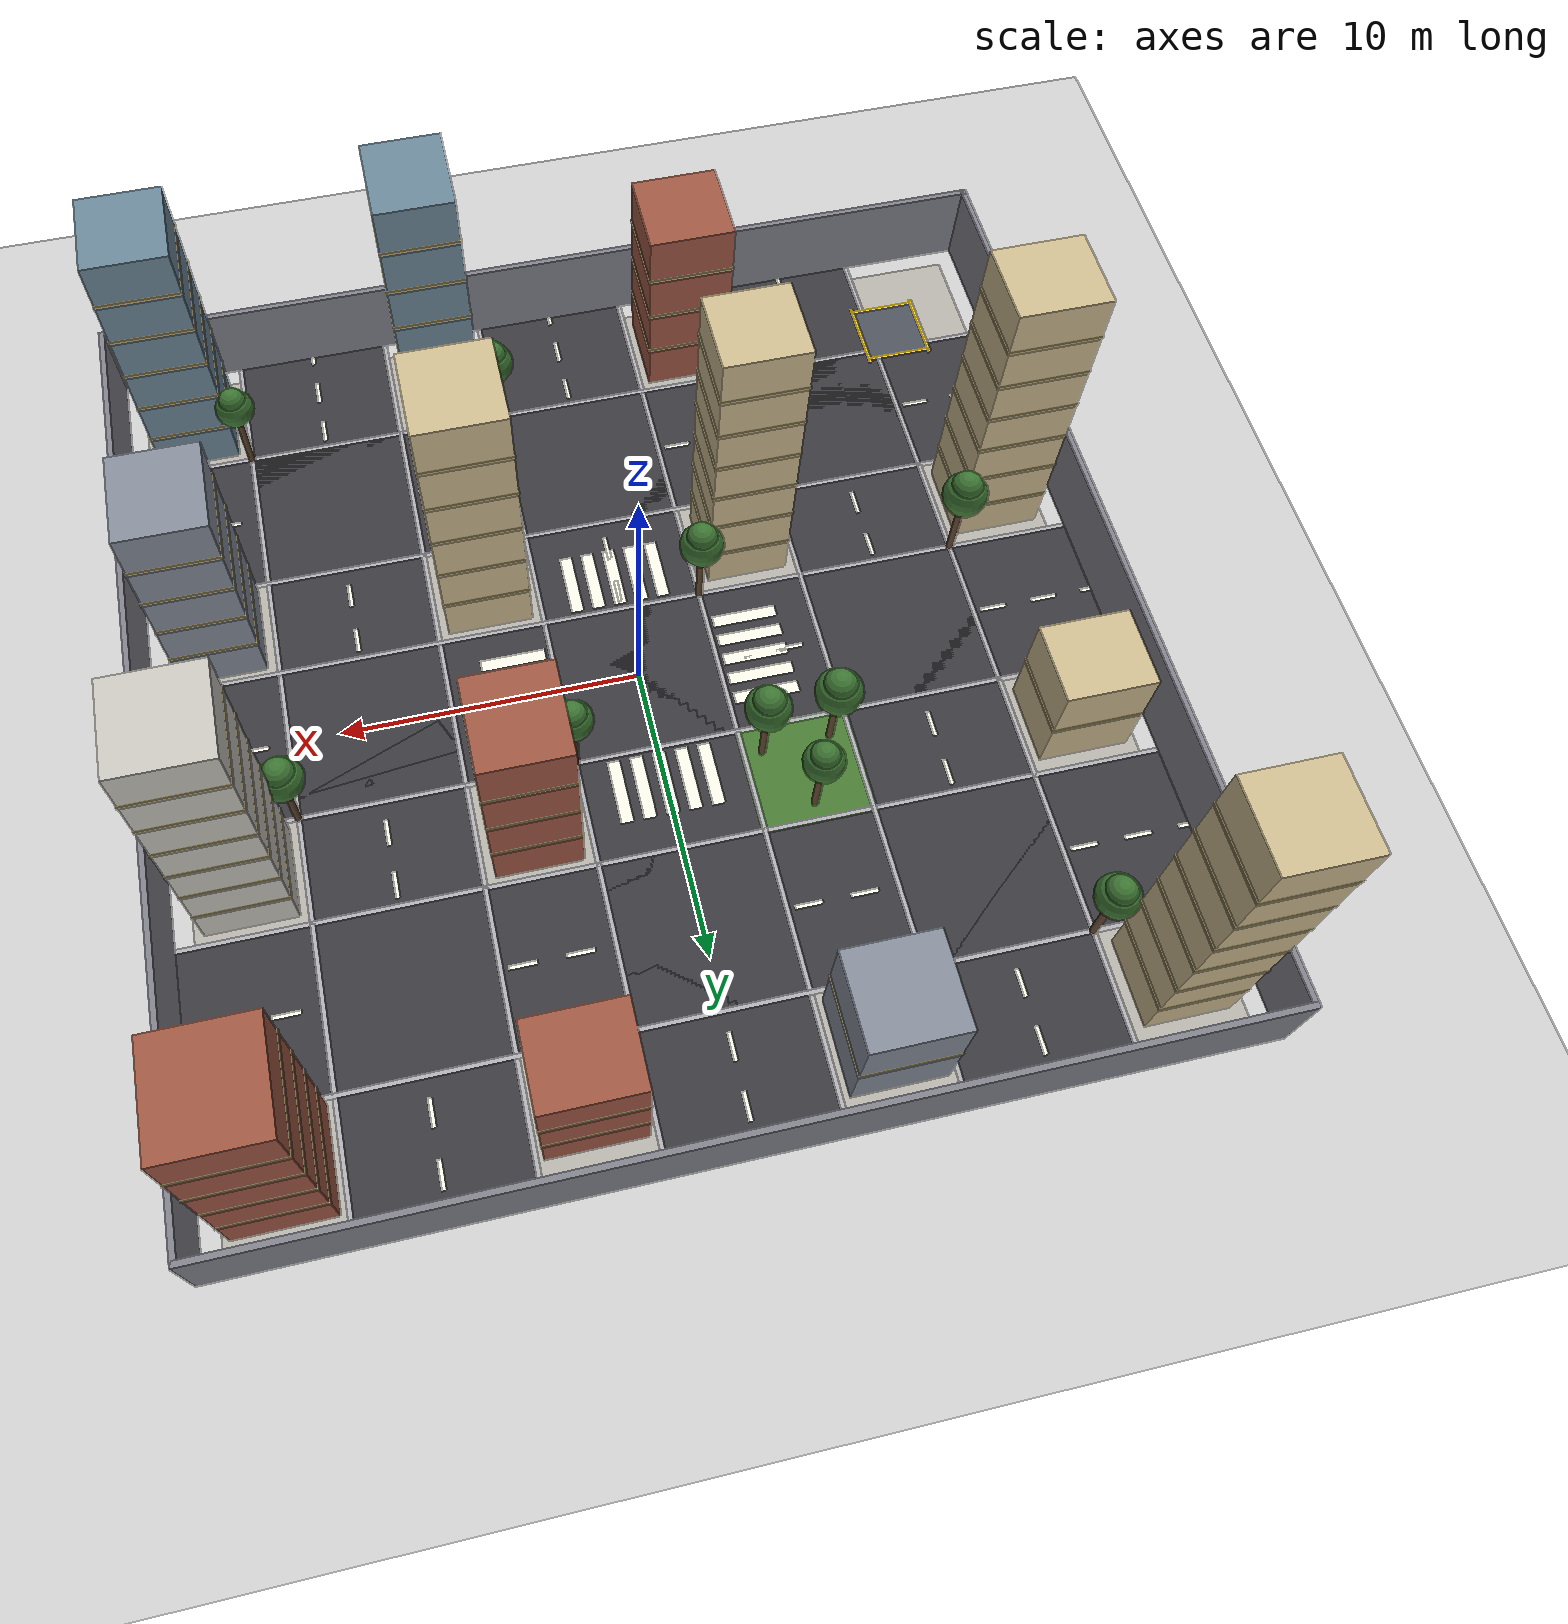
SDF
<?xml version="1.0"?>
<sdf version="1.6">
  <world name="default">

    <include><uri>model://sun</uri></include>
    <include><uri>model://ground_plane</uri></include>

    <plugin name="ros_link_attacher_plugin" filename="libgazebo_ros_link_attacher.so" />

    <scene>
      <ambient>0.65 0.65 0.65 1</ambient>
      <background>0.7 0.8 0.9 1</background>
      <shadows>false</shadows>
    </scene>

    <physics type="ode">
      <max_step_size>0.001</max_step_size>
      <real_time_update_rate>1000</real_time_update_rate>
    </physics>

    <model name="road_ns_0">
      <static>true</static><pose>-9.0000 0.0000 0.0010 0 0 0</pose>
      <link name="link">
        <visual name="v"><geometry><box><size>5.400 32.000 0.002</size></box></geometry>
          <material><ambient>0.13 0.13 0.14 1</ambient><diffuse>0.22 0.22 0.24 1</diffuse></material></visual>
      </link>
    </model>
    <model name="road_ew_0">
      <static>true</static><pose>0.0000 -9.0000 0.0010 0 0 0</pose>
      <link name="link">
        <visual name="v"><geometry><box><size>32.000 5.400 0.002</size></box></geometry>
          <material><ambient>0.13 0.13 0.14 1</ambient><diffuse>0.22 0.22 0.24 1</diffuse></material></visual>
      </link>
    </model>
    <model name="kerb_ns_0_-1">
      <static>true</static><pose>-11.7000 0.0000 0.0030 0 0 0</pose>
      <link name="link">
        <visual name="v"><geometry><box><size>0.160 32.000 0.002</size></box></geometry>
          <material><ambient>0.42 0.42 0.44 1</ambient><diffuse>0.68 0.68 0.70 1</diffuse></material></visual>
      </link>
    </model>
    <model name="kerb_ew_0_-1">
      <static>true</static><pose>0.0000 -11.7000 0.0030 0 0 0</pose>
      <link name="link">
        <visual name="v"><geometry><box><size>32.000 0.160 0.002</size></box></geometry>
          <material><ambient>0.42 0.42 0.44 1</ambient><diffuse>0.68 0.68 0.70 1</diffuse></material></visual>
      </link>
    </model>
    <model name="kerb_ns_0_1">
      <static>true</static><pose>-6.3000 0.0000 0.0030 0 0 0</pose>
      <link name="link">
        <visual name="v"><geometry><box><size>0.160 32.000 0.002</size></box></geometry>
          <material><ambient>0.42 0.42 0.44 1</ambient><diffuse>0.68 0.68 0.70 1</diffuse></material></visual>
      </link>
    </model>
    <model name="kerb_ew_0_1">
      <static>true</static><pose>0.0000 -6.3000 0.0030 0 0 0</pose>
      <link name="link">
        <visual name="v"><geometry><box><size>32.000 0.160 0.002</size></box></geometry>
          <material><ambient>0.42 0.42 0.44 1</ambient><diffuse>0.68 0.68 0.70 1</diffuse></material></visual>
      </link>
    </model>
    <model name="road_ns_1">
      <static>true</static><pose>0.0000 0.0000 0.0010 0 0 0</pose>
      <link name="link">
        <visual name="v"><geometry><box><size>5.400 32.000 0.002</size></box></geometry>
          <material><ambient>0.13 0.13 0.14 1</ambient><diffuse>0.22 0.22 0.24 1</diffuse></material></visual>
      </link>
    </model>
    <model name="road_ew_1">
      <static>true</static><pose>0.0000 0.0000 0.0010 0 0 0</pose>
      <link name="link">
        <visual name="v"><geometry><box><size>32.000 5.400 0.002</size></box></geometry>
          <material><ambient>0.13 0.13 0.14 1</ambient><diffuse>0.22 0.22 0.24 1</diffuse></material></visual>
      </link>
    </model>
    <model name="kerb_ns_1_-1">
      <static>true</static><pose>-2.7000 0.0000 0.0030 0 0 0</pose>
      <link name="link">
        <visual name="v"><geometry><box><size>0.160 32.000 0.002</size></box></geometry>
          <material><ambient>0.42 0.42 0.44 1</ambient><diffuse>0.68 0.68 0.70 1</diffuse></material></visual>
      </link>
    </model>
    <model name="kerb_ew_1_-1">
      <static>true</static><pose>0.0000 -2.7000 0.0030 0 0 0</pose>
      <link name="link">
        <visual name="v"><geometry><box><size>32.000 0.160 0.002</size></box></geometry>
          <material><ambient>0.42 0.42 0.44 1</ambient><diffuse>0.68 0.68 0.70 1</diffuse></material></visual>
      </link>
    </model>
    <model name="kerb_ns_1_1">
      <static>true</static><pose>2.7000 0.0000 0.0030 0 0 0</pose>
      <link name="link">
        <visual name="v"><geometry><box><size>0.160 32.000 0.002</size></box></geometry>
          <material><ambient>0.42 0.42 0.44 1</ambient><diffuse>0.68 0.68 0.70 1</diffuse></material></visual>
      </link>
    </model>
    <model name="kerb_ew_1_1">
      <static>true</static><pose>0.0000 2.7000 0.0030 0 0 0</pose>
      <link name="link">
        <visual name="v"><geometry><box><size>32.000 0.160 0.002</size></box></geometry>
          <material><ambient>0.42 0.42 0.44 1</ambient><diffuse>0.68 0.68 0.70 1</diffuse></material></visual>
      </link>
    </model>
    <model name="road_ns_2">
      <static>true</static><pose>9.0000 0.0000 0.0010 0 0 0</pose>
      <link name="link">
        <visual name="v"><geometry><box><size>5.400 32.000 0.002</size></box></geometry>
          <material><ambient>0.13 0.13 0.14 1</ambient><diffuse>0.22 0.22 0.24 1</diffuse></material></visual>
      </link>
    </model>
    <model name="road_ew_2">
      <static>true</static><pose>0.0000 9.0000 0.0010 0 0 0</pose>
      <link name="link">
        <visual name="v"><geometry><box><size>32.000 5.400 0.002</size></box></geometry>
          <material><ambient>0.13 0.13 0.14 1</ambient><diffuse>0.22 0.22 0.24 1</diffuse></material></visual>
      </link>
    </model>
    <model name="kerb_ns_2_-1">
      <static>true</static><pose>6.3000 0.0000 0.0030 0 0 0</pose>
      <link name="link">
        <visual name="v"><geometry><box><size>0.160 32.000 0.002</size></box></geometry>
          <material><ambient>0.42 0.42 0.44 1</ambient><diffuse>0.68 0.68 0.70 1</diffuse></material></visual>
      </link>
    </model>
    <model name="kerb_ew_2_-1">
      <static>true</static><pose>0.0000 6.3000 0.0030 0 0 0</pose>
      <link name="link">
        <visual name="v"><geometry><box><size>32.000 0.160 0.002</size></box></geometry>
          <material><ambient>0.42 0.42 0.44 1</ambient><diffuse>0.68 0.68 0.70 1</diffuse></material></visual>
      </link>
    </model>
    <model name="kerb_ns_2_1">
      <static>true</static><pose>11.7000 0.0000 0.0030 0 0 0</pose>
      <link name="link">
        <visual name="v"><geometry><box><size>0.160 32.000 0.002</size></box></geometry>
          <material><ambient>0.42 0.42 0.44 1</ambient><diffuse>0.68 0.68 0.70 1</diffuse></material></visual>
      </link>
    </model>
    <model name="kerb_ew_2_1">
      <static>true</static><pose>0.0000 11.7000 0.0030 0 0 0</pose>
      <link name="link">
        <visual name="v"><geometry><box><size>32.000 0.160 0.002</size></box></geometry>
          <material><ambient>0.42 0.42 0.44 1</ambient><diffuse>0.68 0.68 0.70 1</diffuse></material></visual>
      </link>
    </model>
    <model name="dash_ns_0">
      <static>true</static><pose>-9.0000 -16.0000 0.0035 0 0 0</pose>
      <link name="link">
        <visual name="v"><geometry><box><size>0.140 0.900 0.002</size></box></geometry>
          <material><ambient>0.60 0.60 0.55 1</ambient><diffuse>0.95 0.95 0.90 1</diffuse></material></visual>
      </link>
    </model>
    <model name="dash_ns_1">
      <static>true</static><pose>-9.0000 -14.2000 0.0035 0 0 0</pose>
      <link name="link">
        <visual name="v"><geometry><box><size>0.140 0.900 0.002</size></box></geometry>
          <material><ambient>0.60 0.60 0.55 1</ambient><diffuse>0.95 0.95 0.90 1</diffuse></material></visual>
      </link>
    </model>
    <model name="dash_ns_2">
      <static>true</static><pose>-9.0000 -12.4000 0.0035 0 0 0</pose>
      <link name="link">
        <visual name="v"><geometry><box><size>0.140 0.900 0.002</size></box></geometry>
          <material><ambient>0.60 0.60 0.55 1</ambient><diffuse>0.95 0.95 0.90 1</diffuse></material></visual>
      </link>
    </model>
    <model name="dash_ns_3">
      <static>true</static><pose>-9.0000 -5.2000 0.0035 0 0 0</pose>
      <link name="link">
        <visual name="v"><geometry><box><size>0.140 0.900 0.002</size></box></geometry>
          <material><ambient>0.60 0.60 0.55 1</ambient><diffuse>0.95 0.95 0.90 1</diffuse></material></visual>
      </link>
    </model>
    <model name="dash_ns_4">
      <static>true</static><pose>-9.0000 -3.4000 0.0035 0 0 0</pose>
      <link name="link">
        <visual name="v"><geometry><box><size>0.140 0.900 0.002</size></box></geometry>
          <material><ambient>0.60 0.60 0.55 1</ambient><diffuse>0.95 0.95 0.90 1</diffuse></material></visual>
      </link>
    </model>
    <model name="dash_ns_5">
      <static>true</static><pose>-9.0000 3.8000 0.0035 0 0 0</pose>
      <link name="link">
        <visual name="v"><geometry><box><size>0.140 0.900 0.002</size></box></geometry>
          <material><ambient>0.60 0.60 0.55 1</ambient><diffuse>0.95 0.95 0.90 1</diffuse></material></visual>
      </link>
    </model>
    <model name="dash_ns_6">
      <static>true</static><pose>-9.0000 5.6000 0.0035 0 0 0</pose>
      <link name="link">
        <visual name="v"><geometry><box><size>0.140 0.900 0.002</size></box></geometry>
          <material><ambient>0.60 0.60 0.55 1</ambient><diffuse>0.95 0.95 0.90 1</diffuse></material></visual>
      </link>
    </model>
    <model name="dash_ns_7">
      <static>true</static><pose>-9.0000 12.8000 0.0035 0 0 0</pose>
      <link name="link">
        <visual name="v"><geometry><box><size>0.140 0.900 0.002</size></box></geometry>
          <material><ambient>0.60 0.60 0.55 1</ambient><diffuse>0.95 0.95 0.90 1</diffuse></material></visual>
      </link>
    </model>
    <model name="dash_ns_8">
      <static>true</static><pose>-9.0000 14.6000 0.0035 0 0 0</pose>
      <link name="link">
        <visual name="v"><geometry><box><size>0.140 0.900 0.002</size></box></geometry>
          <material><ambient>0.60 0.60 0.55 1</ambient><diffuse>0.95 0.95 0.90 1</diffuse></material></visual>
      </link>
    </model>
    <model name="dash_ew_9">
      <static>true</static><pose>-16.0000 -9.0000 0.0035 0 0 0</pose>
      <link name="link">
        <visual name="v"><geometry><box><size>0.900 0.140 0.002</size></box></geometry>
          <material><ambient>0.60 0.60 0.55 1</ambient><diffuse>0.95 0.95 0.90 1</diffuse></material></visual>
      </link>
    </model>
    <model name="dash_ew_10">
      <static>true</static><pose>-14.2000 -9.0000 0.0035 0 0 0</pose>
      <link name="link">
        <visual name="v"><geometry><box><size>0.900 0.140 0.002</size></box></geometry>
          <material><ambient>0.60 0.60 0.55 1</ambient><diffuse>0.95 0.95 0.90 1</diffuse></material></visual>
      </link>
    </model>
    <model name="dash_ew_11">
      <static>true</static><pose>-12.4000 -9.0000 0.0035 0 0 0</pose>
      <link name="link">
        <visual name="v"><geometry><box><size>0.900 0.140 0.002</size></box></geometry>
          <material><ambient>0.60 0.60 0.55 1</ambient><diffuse>0.95 0.95 0.90 1</diffuse></material></visual>
      </link>
    </model>
    <model name="dash_ew_12">
      <static>true</static><pose>-5.2000 -9.0000 0.0035 0 0 0</pose>
      <link name="link">
        <visual name="v"><geometry><box><size>0.900 0.140 0.002</size></box></geometry>
          <material><ambient>0.60 0.60 0.55 1</ambient><diffuse>0.95 0.95 0.90 1</diffuse></material></visual>
      </link>
    </model>
    <model name="dash_ew_13">
      <static>true</static><pose>-3.4000 -9.0000 0.0035 0 0 0</pose>
      <link name="link">
        <visual name="v"><geometry><box><size>0.900 0.140 0.002</size></box></geometry>
          <material><ambient>0.60 0.60 0.55 1</ambient><diffuse>0.95 0.95 0.90 1</diffuse></material></visual>
      </link>
    </model>
    <model name="dash_ew_14">
      <static>true</static><pose>3.8000 -9.0000 0.0035 0 0 0</pose>
      <link name="link">
        <visual name="v"><geometry><box><size>0.900 0.140 0.002</size></box></geometry>
          <material><ambient>0.60 0.60 0.55 1</ambient><diffuse>0.95 0.95 0.90 1</diffuse></material></visual>
      </link>
    </model>
    <model name="dash_ew_15">
      <static>true</static><pose>5.6000 -9.0000 0.0035 0 0 0</pose>
      <link name="link">
        <visual name="v"><geometry><box><size>0.900 0.140 0.002</size></box></geometry>
          <material><ambient>0.60 0.60 0.55 1</ambient><diffuse>0.95 0.95 0.90 1</diffuse></material></visual>
      </link>
    </model>
    <model name="dash_ew_16">
      <static>true</static><pose>12.8000 -9.0000 0.0035 0 0 0</pose>
      <link name="link">
        <visual name="v"><geometry><box><size>0.900 0.140 0.002</size></box></geometry>
          <material><ambient>0.60 0.60 0.55 1</ambient><diffuse>0.95 0.95 0.90 1</diffuse></material></visual>
      </link>
    </model>
    <model name="dash_ew_17">
      <static>true</static><pose>14.6000 -9.0000 0.0035 0 0 0</pose>
      <link name="link">
        <visual name="v"><geometry><box><size>0.900 0.140 0.002</size></box></geometry>
          <material><ambient>0.60 0.60 0.55 1</ambient><diffuse>0.95 0.95 0.90 1</diffuse></material></visual>
      </link>
    </model>
    <model name="dash_ns_18">
      <static>true</static><pose>0.0000 -16.0000 0.0035 0 0 0</pose>
      <link name="link">
        <visual name="v"><geometry><box><size>0.140 0.900 0.002</size></box></geometry>
          <material><ambient>0.60 0.60 0.55 1</ambient><diffuse>0.95 0.95 0.90 1</diffuse></material></visual>
      </link>
    </model>
    <model name="dash_ns_19">
      <static>true</static><pose>0.0000 -14.2000 0.0035 0 0 0</pose>
      <link name="link">
        <visual name="v"><geometry><box><size>0.140 0.900 0.002</size></box></geometry>
          <material><ambient>0.60 0.60 0.55 1</ambient><diffuse>0.95 0.95 0.90 1</diffuse></material></visual>
      </link>
    </model>
    <model name="dash_ns_20">
      <static>true</static><pose>0.0000 -12.4000 0.0035 0 0 0</pose>
      <link name="link">
        <visual name="v"><geometry><box><size>0.140 0.900 0.002</size></box></geometry>
          <material><ambient>0.60 0.60 0.55 1</ambient><diffuse>0.95 0.95 0.90 1</diffuse></material></visual>
      </link>
    </model>
    <model name="dash_ns_21">
      <static>true</static><pose>0.0000 -5.2000 0.0035 0 0 0</pose>
      <link name="link">
        <visual name="v"><geometry><box><size>0.140 0.900 0.002</size></box></geometry>
          <material><ambient>0.60 0.60 0.55 1</ambient><diffuse>0.95 0.95 0.90 1</diffuse></material></visual>
      </link>
    </model>
    <model name="dash_ns_22">
      <static>true</static><pose>0.0000 -3.4000 0.0035 0 0 0</pose>
      <link name="link">
        <visual name="v"><geometry><box><size>0.140 0.900 0.002</size></box></geometry>
          <material><ambient>0.60 0.60 0.55 1</ambient><diffuse>0.95 0.95 0.90 1</diffuse></material></visual>
      </link>
    </model>
    <model name="dash_ns_23">
      <static>true</static><pose>0.0000 3.8000 0.0035 0 0 0</pose>
      <link name="link">
        <visual name="v"><geometry><box><size>0.140 0.900 0.002</size></box></geometry>
          <material><ambient>0.60 0.60 0.55 1</ambient><diffuse>0.95 0.95 0.90 1</diffuse></material></visual>
      </link>
    </model>
    <model name="dash_ns_24">
      <static>true</static><pose>0.0000 5.6000 0.0035 0 0 0</pose>
      <link name="link">
        <visual name="v"><geometry><box><size>0.140 0.900 0.002</size></box></geometry>
          <material><ambient>0.60 0.60 0.55 1</ambient><diffuse>0.95 0.95 0.90 1</diffuse></material></visual>
      </link>
    </model>
    <model name="dash_ns_25">
      <static>true</static><pose>0.0000 12.8000 0.0035 0 0 0</pose>
      <link name="link">
        <visual name="v"><geometry><box><size>0.140 0.900 0.002</size></box></geometry>
          <material><ambient>0.60 0.60 0.55 1</ambient><diffuse>0.95 0.95 0.90 1</diffuse></material></visual>
      </link>
    </model>
    <model name="dash_ns_26">
      <static>true</static><pose>0.0000 14.6000 0.0035 0 0 0</pose>
      <link name="link">
        <visual name="v"><geometry><box><size>0.140 0.900 0.002</size></box></geometry>
          <material><ambient>0.60 0.60 0.55 1</ambient><diffuse>0.95 0.95 0.90 1</diffuse></material></visual>
      </link>
    </model>
    <model name="dash_ew_27">
      <static>true</static><pose>-16.0000 0.0000 0.0035 0 0 0</pose>
      <link name="link">
        <visual name="v"><geometry><box><size>0.900 0.140 0.002</size></box></geometry>
          <material><ambient>0.60 0.60 0.55 1</ambient><diffuse>0.95 0.95 0.90 1</diffuse></material></visual>
      </link>
    </model>
    <model name="dash_ew_28">
      <static>true</static><pose>-14.2000 0.0000 0.0035 0 0 0</pose>
      <link name="link">
        <visual name="v"><geometry><box><size>0.900 0.140 0.002</size></box></geometry>
          <material><ambient>0.60 0.60 0.55 1</ambient><diffuse>0.95 0.95 0.90 1</diffuse></material></visual>
      </link>
    </model>
    <model name="dash_ew_29">
      <static>true</static><pose>-12.4000 0.0000 0.0035 0 0 0</pose>
      <link name="link">
        <visual name="v"><geometry><box><size>0.900 0.140 0.002</size></box></geometry>
          <material><ambient>0.60 0.60 0.55 1</ambient><diffuse>0.95 0.95 0.90 1</diffuse></material></visual>
      </link>
    </model>
    <model name="dash_ew_30">
      <static>true</static><pose>-5.2000 0.0000 0.0035 0 0 0</pose>
      <link name="link">
        <visual name="v"><geometry><box><size>0.900 0.140 0.002</size></box></geometry>
          <material><ambient>0.60 0.60 0.55 1</ambient><diffuse>0.95 0.95 0.90 1</diffuse></material></visual>
      </link>
    </model>
    <model name="dash_ew_31">
      <static>true</static><pose>-3.4000 0.0000 0.0035 0 0 0</pose>
      <link name="link">
        <visual name="v"><geometry><box><size>0.900 0.140 0.002</size></box></geometry>
          <material><ambient>0.60 0.60 0.55 1</ambient><diffuse>0.95 0.95 0.90 1</diffuse></material></visual>
      </link>
    </model>
    <model name="dash_ew_32">
      <static>true</static><pose>3.8000 0.0000 0.0035 0 0 0</pose>
      <link name="link">
        <visual name="v"><geometry><box><size>0.900 0.140 0.002</size></box></geometry>
          <material><ambient>0.60 0.60 0.55 1</ambient><diffuse>0.95 0.95 0.90 1</diffuse></material></visual>
      </link>
    </model>
    <model name="dash_ew_33">
      <static>true</static><pose>5.6000 0.0000 0.0035 0 0 0</pose>
      <link name="link">
        <visual name="v"><geometry><box><size>0.900 0.140 0.002</size></box></geometry>
          <material><ambient>0.60 0.60 0.55 1</ambient><diffuse>0.95 0.95 0.90 1</diffuse></material></visual>
      </link>
    </model>
    <model name="dash_ew_34">
      <static>true</static><pose>12.8000 0.0000 0.0035 0 0 0</pose>
      <link name="link">
        <visual name="v"><geometry><box><size>0.900 0.140 0.002</size></box></geometry>
          <material><ambient>0.60 0.60 0.55 1</ambient><diffuse>0.95 0.95 0.90 1</diffuse></material></visual>
      </link>
    </model>
    <model name="dash_ew_35">
      <static>true</static><pose>14.6000 0.0000 0.0035 0 0 0</pose>
      <link name="link">
        <visual name="v"><geometry><box><size>0.900 0.140 0.002</size></box></geometry>
          <material><ambient>0.60 0.60 0.55 1</ambient><diffuse>0.95 0.95 0.90 1</diffuse></material></visual>
      </link>
    </model>
    <model name="dash_ns_36">
      <static>true</static><pose>9.0000 -16.0000 0.0035 0 0 0</pose>
      <link name="link">
        <visual name="v"><geometry><box><size>0.140 0.900 0.002</size></box></geometry>
          <material><ambient>0.60 0.60 0.55 1</ambient><diffuse>0.95 0.95 0.90 1</diffuse></material></visual>
      </link>
    </model>
    <model name="dash_ns_37">
      <static>true</static><pose>9.0000 -14.2000 0.0035 0 0 0</pose>
      <link name="link">
        <visual name="v"><geometry><box><size>0.140 0.900 0.002</size></box></geometry>
          <material><ambient>0.60 0.60 0.55 1</ambient><diffuse>0.95 0.95 0.90 1</diffuse></material></visual>
      </link>
    </model>
    <model name="dash_ns_38">
      <static>true</static><pose>9.0000 -12.4000 0.0035 0 0 0</pose>
      <link name="link">
        <visual name="v"><geometry><box><size>0.140 0.900 0.002</size></box></geometry>
          <material><ambient>0.60 0.60 0.55 1</ambient><diffuse>0.95 0.95 0.90 1</diffuse></material></visual>
      </link>
    </model>
    <model name="dash_ns_39">
      <static>true</static><pose>9.0000 -5.2000 0.0035 0 0 0</pose>
      <link name="link">
        <visual name="v"><geometry><box><size>0.140 0.900 0.002</size></box></geometry>
          <material><ambient>0.60 0.60 0.55 1</ambient><diffuse>0.95 0.95 0.90 1</diffuse></material></visual>
      </link>
    </model>
    <model name="dash_ns_40">
      <static>true</static><pose>9.0000 -3.4000 0.0035 0 0 0</pose>
      <link name="link">
        <visual name="v"><geometry><box><size>0.140 0.900 0.002</size></box></geometry>
          <material><ambient>0.60 0.60 0.55 1</ambient><diffuse>0.95 0.95 0.90 1</diffuse></material></visual>
      </link>
    </model>
    <model name="dash_ns_41">
      <static>true</static><pose>9.0000 3.8000 0.0035 0 0 0</pose>
      <link name="link">
        <visual name="v"><geometry><box><size>0.140 0.900 0.002</size></box></geometry>
          <material><ambient>0.60 0.60 0.55 1</ambient><diffuse>0.95 0.95 0.90 1</diffuse></material></visual>
      </link>
    </model>
    <model name="dash_ns_42">
      <static>true</static><pose>9.0000 5.6000 0.0035 0 0 0</pose>
      <link name="link">
        <visual name="v"><geometry><box><size>0.140 0.900 0.002</size></box></geometry>
          <material><ambient>0.60 0.60 0.55 1</ambient><diffuse>0.95 0.95 0.90 1</diffuse></material></visual>
      </link>
    </model>
    <model name="dash_ns_43">
      <static>true</static><pose>9.0000 12.8000 0.0035 0 0 0</pose>
      <link name="link">
        <visual name="v"><geometry><box><size>0.140 0.900 0.002</size></box></geometry>
          <material><ambient>0.60 0.60 0.55 1</ambient><diffuse>0.95 0.95 0.90 1</diffuse></material></visual>
      </link>
    </model>
    <model name="dash_ns_44">
      <static>true</static><pose>9.0000 14.6000 0.0035 0 0 0</pose>
      <link name="link">
        <visual name="v"><geometry><box><size>0.140 0.900 0.002</size></box></geometry>
          <material><ambient>0.60 0.60 0.55 1</ambient><diffuse>0.95 0.95 0.90 1</diffuse></material></visual>
      </link>
    </model>
    <model name="dash_ew_45">
      <static>true</static><pose>-16.0000 9.0000 0.0035 0 0 0</pose>
      <link name="link">
        <visual name="v"><geometry><box><size>0.900 0.140 0.002</size></box></geometry>
          <material><ambient>0.60 0.60 0.55 1</ambient><diffuse>0.95 0.95 0.90 1</diffuse></material></visual>
      </link>
    </model>
    <model name="dash_ew_46">
      <static>true</static><pose>-14.2000 9.0000 0.0035 0 0 0</pose>
      <link name="link">
        <visual name="v"><geometry><box><size>0.900 0.140 0.002</size></box></geometry>
          <material><ambient>0.60 0.60 0.55 1</ambient><diffuse>0.95 0.95 0.90 1</diffuse></material></visual>
      </link>
    </model>
    <model name="dash_ew_47">
      <static>true</static><pose>-12.4000 9.0000 0.0035 0 0 0</pose>
      <link name="link">
        <visual name="v"><geometry><box><size>0.900 0.140 0.002</size></box></geometry>
          <material><ambient>0.60 0.60 0.55 1</ambient><diffuse>0.95 0.95 0.90 1</diffuse></material></visual>
      </link>
    </model>
    <model name="dash_ew_48">
      <static>true</static><pose>-5.2000 9.0000 0.0035 0 0 0</pose>
      <link name="link">
        <visual name="v"><geometry><box><size>0.900 0.140 0.002</size></box></geometry>
          <material><ambient>0.60 0.60 0.55 1</ambient><diffuse>0.95 0.95 0.90 1</diffuse></material></visual>
      </link>
    </model>
    <model name="dash_ew_49">
      <static>true</static><pose>-3.4000 9.0000 0.0035 0 0 0</pose>
      <link name="link">
        <visual name="v"><geometry><box><size>0.900 0.140 0.002</size></box></geometry>
          <material><ambient>0.60 0.60 0.55 1</ambient><diffuse>0.95 0.95 0.90 1</diffuse></material></visual>
      </link>
    </model>
    <model name="dash_ew_50">
      <static>true</static><pose>3.8000 9.0000 0.0035 0 0 0</pose>
      <link name="link">
        <visual name="v"><geometry><box><size>0.900 0.140 0.002</size></box></geometry>
          <material><ambient>0.60 0.60 0.55 1</ambient><diffuse>0.95 0.95 0.90 1</diffuse></material></visual>
      </link>
    </model>
    <model name="dash_ew_51">
      <static>true</static><pose>5.6000 9.0000 0.0035 0 0 0</pose>
      <link name="link">
        <visual name="v"><geometry><box><size>0.900 0.140 0.002</size></box></geometry>
          <material><ambient>0.60 0.60 0.55 1</ambient><diffuse>0.95 0.95 0.90 1</diffuse></material></visual>
      </link>
    </model>
    <model name="dash_ew_52">
      <static>true</static><pose>12.8000 9.0000 0.0035 0 0 0</pose>
      <link name="link">
        <visual name="v"><geometry><box><size>0.900 0.140 0.002</size></box></geometry>
          <material><ambient>0.60 0.60 0.55 1</ambient><diffuse>0.95 0.95 0.90 1</diffuse></material></visual>
      </link>
    </model>
    <model name="dash_ew_53">
      <static>true</static><pose>14.6000 9.0000 0.0035 0 0 0</pose>
      <link name="link">
        <visual name="v"><geometry><box><size>0.900 0.140 0.002</size></box></geometry>
          <material><ambient>0.60 0.60 0.55 1</ambient><diffuse>0.95 0.95 0.90 1</diffuse></material></visual>
      </link>
    </model>
    <model name="zebra_0">
      <static>true</static><pose>-1.5000 4.0000 0.0035 0 0 0</pose>
      <link name="link">
        <visual name="v"><geometry><box><size>0.420 2.200 0.002</size></box></geometry>
          <material><ambient>0.60 0.60 0.55 1</ambient><diffuse>0.95 0.95 0.90 1</diffuse></material></visual>
      </link>
    </model>
    <model name="zebra_1">
      <static>true</static><pose>-0.7500 4.0000 0.0035 0 0 0</pose>
      <link name="link">
        <visual name="v"><geometry><box><size>0.420 2.200 0.002</size></box></geometry>
          <material><ambient>0.60 0.60 0.55 1</ambient><diffuse>0.95 0.95 0.90 1</diffuse></material></visual>
      </link>
    </model>
    <model name="zebra_2">
      <static>true</static><pose>0.0000 4.0000 0.0035 0 0 0</pose>
      <link name="link">
        <visual name="v"><geometry><box><size>0.420 2.200 0.002</size></box></geometry>
          <material><ambient>0.60 0.60 0.55 1</ambient><diffuse>0.95 0.95 0.90 1</diffuse></material></visual>
      </link>
    </model>
    <model name="zebra_3">
      <static>true</static><pose>0.7500 4.0000 0.0035 0 0 0</pose>
      <link name="link">
        <visual name="v"><geometry><box><size>0.420 2.200 0.002</size></box></geometry>
          <material><ambient>0.60 0.60 0.55 1</ambient><diffuse>0.95 0.95 0.90 1</diffuse></material></visual>
      </link>
    </model>
    <model name="zebra_4">
      <static>true</static><pose>1.5000 4.0000 0.0035 0 0 0</pose>
      <link name="link">
        <visual name="v"><geometry><box><size>0.420 2.200 0.002</size></box></geometry>
          <material><ambient>0.60 0.60 0.55 1</ambient><diffuse>0.95 0.95 0.90 1</diffuse></material></visual>
      </link>
    </model>
    <model name="zebra_5">
      <static>true</static><pose>-1.5000 -4.0000 0.0035 0 0 0</pose>
      <link name="link">
        <visual name="v"><geometry><box><size>0.420 2.200 0.002</size></box></geometry>
          <material><ambient>0.60 0.60 0.55 1</ambient><diffuse>0.95 0.95 0.90 1</diffuse></material></visual>
      </link>
    </model>
    <model name="zebra_6">
      <static>true</static><pose>-0.7500 -4.0000 0.0035 0 0 0</pose>
      <link name="link">
        <visual name="v"><geometry><box><size>0.420 2.200 0.002</size></box></geometry>
          <material><ambient>0.60 0.60 0.55 1</ambient><diffuse>0.95 0.95 0.90 1</diffuse></material></visual>
      </link>
    </model>
    <model name="zebra_7">
      <static>true</static><pose>0.0000 -4.0000 0.0035 0 0 0</pose>
      <link name="link">
        <visual name="v"><geometry><box><size>0.420 2.200 0.002</size></box></geometry>
          <material><ambient>0.60 0.60 0.55 1</ambient><diffuse>0.95 0.95 0.90 1</diffuse></material></visual>
      </link>
    </model>
    <model name="zebra_8">
      <static>true</static><pose>0.7500 -4.0000 0.0035 0 0 0</pose>
      <link name="link">
        <visual name="v"><geometry><box><size>0.420 2.200 0.002</size></box></geometry>
          <material><ambient>0.60 0.60 0.55 1</ambient><diffuse>0.95 0.95 0.90 1</diffuse></material></visual>
      </link>
    </model>
    <model name="zebra_9">
      <static>true</static><pose>1.5000 -4.0000 0.0035 0 0 0</pose>
      <link name="link">
        <visual name="v"><geometry><box><size>0.420 2.200 0.002</size></box></geometry>
          <material><ambient>0.60 0.60 0.55 1</ambient><diffuse>0.95 0.95 0.90 1</diffuse></material></visual>
      </link>
    </model>
    <model name="zebra_10">
      <static>true</static><pose>4.0000 -1.5000 0.0035 0 0 0</pose>
      <link name="link">
        <visual name="v"><geometry><box><size>2.200 0.420 0.002</size></box></geometry>
          <material><ambient>0.60 0.60 0.55 1</ambient><diffuse>0.95 0.95 0.90 1</diffuse></material></visual>
      </link>
    </model>
    <model name="zebra_11">
      <static>true</static><pose>4.0000 -0.7500 0.0035 0 0 0</pose>
      <link name="link">
        <visual name="v"><geometry><box><size>2.200 0.420 0.002</size></box></geometry>
          <material><ambient>0.60 0.60 0.55 1</ambient><diffuse>0.95 0.95 0.90 1</diffuse></material></visual>
      </link>
    </model>
    <model name="zebra_12">
      <static>true</static><pose>4.0000 0.0000 0.0035 0 0 0</pose>
      <link name="link">
        <visual name="v"><geometry><box><size>2.200 0.420 0.002</size></box></geometry>
          <material><ambient>0.60 0.60 0.55 1</ambient><diffuse>0.95 0.95 0.90 1</diffuse></material></visual>
      </link>
    </model>
    <model name="zebra_13">
      <static>true</static><pose>4.0000 0.7500 0.0035 0 0 0</pose>
      <link name="link">
        <visual name="v"><geometry><box><size>2.200 0.420 0.002</size></box></geometry>
          <material><ambient>0.60 0.60 0.55 1</ambient><diffuse>0.95 0.95 0.90 1</diffuse></material></visual>
      </link>
    </model>
    <model name="zebra_14">
      <static>true</static><pose>4.0000 1.5000 0.0035 0 0 0</pose>
      <link name="link">
        <visual name="v"><geometry><box><size>2.200 0.420 0.002</size></box></geometry>
          <material><ambient>0.60 0.60 0.55 1</ambient><diffuse>0.95 0.95 0.90 1</diffuse></material></visual>
      </link>
    </model>
    <model name="zebra_15">
      <static>true</static><pose>-4.0000 -1.5000 0.0035 0 0 0</pose>
      <link name="link">
        <visual name="v"><geometry><box><size>2.200 0.420 0.002</size></box></geometry>
          <material><ambient>0.60 0.60 0.55 1</ambient><diffuse>0.95 0.95 0.90 1</diffuse></material></visual>
      </link>
    </model>
    <model name="zebra_16">
      <static>true</static><pose>-4.0000 -0.7500 0.0035 0 0 0</pose>
      <link name="link">
        <visual name="v"><geometry><box><size>2.200 0.420 0.002</size></box></geometry>
          <material><ambient>0.60 0.60 0.55 1</ambient><diffuse>0.95 0.95 0.90 1</diffuse></material></visual>
      </link>
    </model>
    <model name="zebra_17">
      <static>true</static><pose>-4.0000 0.0000 0.0035 0 0 0</pose>
      <link name="link">
        <visual name="v"><geometry><box><size>2.200 0.420 0.002</size></box></geometry>
          <material><ambient>0.60 0.60 0.55 1</ambient><diffuse>0.95 0.95 0.90 1</diffuse></material></visual>
      </link>
    </model>
    <model name="zebra_18">
      <static>true</static><pose>-4.0000 0.7500 0.0035 0 0 0</pose>
      <link name="link">
        <visual name="v"><geometry><box><size>2.200 0.420 0.002</size></box></geometry>
          <material><ambient>0.60 0.60 0.55 1</ambient><diffuse>0.95 0.95 0.90 1</diffuse></material></visual>
      </link>
    </model>
    <model name="zebra_19">
      <static>true</static><pose>-4.0000 1.5000 0.0035 0 0 0</pose>
      <link name="link">
        <visual name="v"><geometry><box><size>2.200 0.420 0.002</size></box></geometry>
          <material><ambient>0.60 0.60 0.55 1</ambient><diffuse>0.95 0.95 0.90 1</diffuse></material></visual>
      </link>
    </model>
    <model name="pavement_00">
      <static>true</static><pose>-13.5000 -4.5000 0.0010 0 0 0</pose>
      <link name="link">
        <visual name="v"><geometry><box><size>3.600 3.600 0.002</size></box></geometry>
          <material><ambient>0.44 0.43 0.41 1</ambient><diffuse>0.70 0.69 0.66 1</diffuse></material></visual>
      </link>
    </model>
    <model name="pavement_01">
      <static>true</static><pose>-13.5000 4.5000 0.0010 0 0 0</pose>
      <link name="link">
        <visual name="v"><geometry><box><size>3.600 3.600 0.002</size></box></geometry>
          <material><ambient>0.44 0.43 0.41 1</ambient><diffuse>0.70 0.69 0.66 1</diffuse></material></visual>
      </link>
    </model>
    <model name="pavement_02">
      <static>true</static><pose>-13.5000 13.5000 0.0010 0 0 0</pose>
      <link name="link">
        <visual name="v"><geometry><box><size>3.600 3.600 0.002</size></box></geometry>
          <material><ambient>0.44 0.43 0.41 1</ambient><diffuse>0.70 0.69 0.66 1</diffuse></material></visual>
      </link>
    </model>
    <model name="pavement_03">
      <static>true</static><pose>-4.5000 -13.5000 0.0010 0 0 0</pose>
      <link name="link">
        <visual name="v"><geometry><box><size>3.600 3.600 0.002</size></box></geometry>
          <material><ambient>0.44 0.43 0.41 1</ambient><diffuse>0.70 0.69 0.66 1</diffuse></material></visual>
      </link>
    </model>
    <model name="pavement_04">
      <static>true</static><pose>-4.5000 -4.5000 0.0010 0 0 0</pose>
      <link name="link">
        <visual name="v"><geometry><box><size>3.600 3.600 0.002</size></box></geometry>
          <material><ambient>0.44 0.43 0.41 1</ambient><diffuse>0.70 0.69 0.66 1</diffuse></material></visual>
      </link>
    </model>
    <model name="pavement_06">
      <static>true</static><pose>-4.5000 13.5000 0.0010 0 0 0</pose>
      <link name="link">
        <visual name="v"><geometry><box><size>3.600 3.600 0.002</size></box></geometry>
          <material><ambient>0.44 0.43 0.41 1</ambient><diffuse>0.70 0.69 0.66 1</diffuse></material></visual>
      </link>
    </model>
    <model name="pavement_07">
      <static>true</static><pose>4.5000 -13.5000 0.0010 0 0 0</pose>
      <link name="link">
        <visual name="v"><geometry><box><size>3.600 3.600 0.002</size></box></geometry>
          <material><ambient>0.44 0.43 0.41 1</ambient><diffuse>0.70 0.69 0.66 1</diffuse></material></visual>
      </link>
    </model>
    <model name="pavement_08">
      <static>true</static><pose>4.5000 -4.5000 0.0010 0 0 0</pose>
      <link name="link">
        <visual name="v"><geometry><box><size>3.600 3.600 0.002</size></box></geometry>
          <material><ambient>0.44 0.43 0.41 1</ambient><diffuse>0.70 0.69 0.66 1</diffuse></material></visual>
      </link>
    </model>
    <model name="pavement_09">
      <static>true</static><pose>4.5000 4.5000 0.0010 0 0 0</pose>
      <link name="link">
        <visual name="v"><geometry><box><size>3.600 3.600 0.002</size></box></geometry>
          <material><ambient>0.44 0.43 0.41 1</ambient><diffuse>0.70 0.69 0.66 1</diffuse></material></visual>
      </link>
    </model>
    <model name="pavement_10">
      <static>true</static><pose>4.5000 13.5000 0.0010 0 0 0</pose>
      <link name="link">
        <visual name="v"><geometry><box><size>3.600 3.600 0.002</size></box></geometry>
          <material><ambient>0.44 0.43 0.41 1</ambient><diffuse>0.70 0.69 0.66 1</diffuse></material></visual>
      </link>
    </model>
    <model name="pavement_11">
      <static>true</static><pose>13.5000 -13.5000 0.0010 0 0 0</pose>
      <link name="link">
        <visual name="v"><geometry><box><size>3.600 3.600 0.002</size></box></geometry>
          <material><ambient>0.44 0.43 0.41 1</ambient><diffuse>0.70 0.69 0.66 1</diffuse></material></visual>
      </link>
    </model>
    <model name="pavement_12">
      <static>true</static><pose>13.5000 -4.5000 0.0010 0 0 0</pose>
      <link name="link">
        <visual name="v"><geometry><box><size>3.600 3.600 0.002</size></box></geometry>
          <material><ambient>0.44 0.43 0.41 1</ambient><diffuse>0.70 0.69 0.66 1</diffuse></material></visual>
      </link>
    </model>
    <model name="pavement_13">
      <static>true</static><pose>13.5000 4.5000 0.0010 0 0 0</pose>
      <link name="link">
        <visual name="v"><geometry><box><size>3.600 3.600 0.002</size></box></geometry>
          <material><ambient>0.44 0.43 0.41 1</ambient><diffuse>0.70 0.69 0.66 1</diffuse></material></visual>
      </link>
    </model>
    <model name="pavement_14">
      <static>true</static><pose>13.5000 13.5000 0.0010 0 0 0</pose>
      <link name="link">
        <visual name="v"><geometry><box><size>3.600 3.600 0.002</size></box></geometry>
          <material><ambient>0.44 0.43 0.41 1</ambient><diffuse>0.70 0.69 0.66 1</diffuse></material></visual>
      </link>
    </model>
    <model name="pavement_15">
      <static>true</static><pose>-13.5000 -13.5000 0.0010 0 0 0</pose>
      <link name="link">
        <visual name="v"><geometry><box><size>3.600 3.600 0.002</size></box></geometry>
          <material><ambient>0.44 0.43 0.41 1</ambient><diffuse>0.70 0.69 0.66 1</diffuse></material></visual>
      </link>
    </model>
    <model name="park_lawn">
      <static>true</static><pose>-4.5000 4.5000 0.0014 0 0 0</pose>
      <link name="link">
        <visual name="v"><geometry><box><size>3.800 3.800 0.002</size></box></geometry>
          <material><ambient>0.16 0.28 0.12 1</ambient><diffuse>0.28 0.48 0.20 1</diffuse></material></visual>
      </link>
    </model>
    <model name="warehouse_apron">
      <static>true</static><pose>-12.5000 -12.5000 0.0040 0 0 0</pose>
      <link name="link">
        <visual name="v"><geometry><box><size>2.400 2.400 0.002</size></box></geometry>
          <material><ambient>0.16 0.16 0.19 1</ambient><diffuse>0.30 0.32 0.36 1</diffuse><emissive>0.09 0.09 0.11 1</emissive></material></visual>
      </link>
    </model>
    <model name="warehouse_edge_n">
      <static>true</static><pose>-12.5000 -11.3500 0.0050 0 0 0</pose>
      <link name="link">
        <visual name="v"><geometry><box><size>2.400 0.120 0.002</size></box></geometry>
          <material><ambient>0.35 0.30 0.05 1</ambient><diffuse>0.95 0.80 0.10 1</diffuse><emissive>0.25 0.21 0.03 1</emissive></material></visual>
      </link>
    </model>
    <model name="warehouse_edge_s">
      <static>true</static><pose>-12.5000 -13.6500 0.0050 0 0 0</pose>
      <link name="link">
        <visual name="v"><geometry><box><size>2.400 0.120 0.002</size></box></geometry>
          <material><ambient>0.35 0.30 0.05 1</ambient><diffuse>0.95 0.80 0.10 1</diffuse><emissive>0.25 0.21 0.03 1</emissive></material></visual>
      </link>
    </model>
    <model name="warehouse_edge_e">
      <static>true</static><pose>-11.3500 -12.5000 0.0050 0 0 0</pose>
      <link name="link">
        <visual name="v"><geometry><box><size>0.120 2.640 0.002</size></box></geometry>
          <material><ambient>0.35 0.30 0.05 1</ambient><diffuse>0.95 0.80 0.10 1</diffuse><emissive>0.25 0.21 0.03 1</emissive></material></visual>
      </link>
    </model>
    <model name="warehouse_edge_w">
      <static>true</static><pose>-13.6500 -12.5000 0.0050 0 0 0</pose>
      <link name="link">
        <visual name="v"><geometry><box><size>0.120 2.640 0.002</size></box></geometry>
          <material><ambient>0.35 0.30 0.05 1</ambient><diffuse>0.95 0.80 0.10 1</diffuse><emissive>0.25 0.21 0.03 1</emissive></material></visual>
      </link>
    </model>
    <model name="building_00">
      <static>true</static><pose>-13.5000 -4.5000 5.6638 0 0 0</pose>
      <link name="link">
        <collision name="c"><geometry><box><size>2.956 2.678 11.328</size></box></geometry></collision>
        <visual name="v"><geometry><box><size>2.956 2.678 11.328</size></box></geometry>
          <material><ambient>0.50 0.45 0.34 1</ambient><diffuse>0.80 0.73 0.56 1</diffuse></material></visual>
      </link>
    </model>
    <model name="building_00_win1">
      <static>true</static><pose>-13.5000 -4.5000 1.6182 0 0 0</pose>
      <link name="link">
        <visual name="v"><geometry><box><size>2.996 2.718 0.140</size></box></geometry>
          <material><ambient>0.30 0.28 0.20 1</ambient><diffuse>0.72 0.66 0.46 1</diffuse><emissive>0.30 0.26 0.15 1</emissive></material></visual>
      </link>
    </model>
    <model name="building_00_win2">
      <static>true</static><pose>-13.5000 -4.5000 3.2364 0 0 0</pose>
      <link name="link">
        <visual name="v"><geometry><box><size>2.996 2.718 0.140</size></box></geometry>
          <material><ambient>0.30 0.28 0.20 1</ambient><diffuse>0.72 0.66 0.46 1</diffuse><emissive>0.30 0.26 0.15 1</emissive></material></visual>
      </link>
    </model>
    <model name="building_00_win3">
      <static>true</static><pose>-13.5000 -4.5000 4.8547 0 0 0</pose>
      <link name="link">
        <visual name="v"><geometry><box><size>2.996 2.718 0.140</size></box></geometry>
          <material><ambient>0.30 0.28 0.20 1</ambient><diffuse>0.72 0.66 0.46 1</diffuse><emissive>0.30 0.26 0.15 1</emissive></material></visual>
      </link>
    </model>
    <model name="building_00_win4">
      <static>true</static><pose>-13.5000 -4.5000 6.4729 0 0 0</pose>
      <link name="link">
        <visual name="v"><geometry><box><size>2.996 2.718 0.140</size></box></geometry>
          <material><ambient>0.30 0.28 0.20 1</ambient><diffuse>0.72 0.66 0.46 1</diffuse><emissive>0.30 0.26 0.15 1</emissive></material></visual>
      </link>
    </model>
    <model name="building_00_win5">
      <static>true</static><pose>-13.5000 -4.5000 8.0911 0 0 0</pose>
      <link name="link">
        <visual name="v"><geometry><box><size>2.996 2.718 0.140</size></box></geometry>
          <material><ambient>0.30 0.28 0.20 1</ambient><diffuse>0.72 0.66 0.46 1</diffuse><emissive>0.30 0.26 0.15 1</emissive></material></visual>
      </link>
    </model>
    <model name="building_00_win6">
      <static>true</static><pose>-13.5000 -4.5000 9.7093 0 0 0</pose>
      <link name="link">
        <visual name="v"><geometry><box><size>2.996 2.718 0.140</size></box></geometry>
          <material><ambient>0.30 0.28 0.20 1</ambient><diffuse>0.72 0.66 0.46 1</diffuse><emissive>0.30 0.26 0.15 1</emissive></material></visual>
      </link>
    </model>
    <model name="building_01">
      <static>true</static><pose>-13.5000 4.5000 2.0527 0 0 0</pose>
      <link name="link">
        <collision name="c"><geometry><box><size>2.975 2.639 4.105</size></box></geometry></collision>
        <visual name="v"><geometry><box><size>2.975 2.639 4.105</size></box></geometry>
          <material><ambient>0.50 0.45 0.34 1</ambient><diffuse>0.80 0.73 0.56 1</diffuse></material></visual>
      </link>
    </model>
    <model name="building_01_win1">
      <static>true</static><pose>-13.5000 4.5000 2.0527 0 0 0</pose>
      <link name="link">
        <visual name="v"><geometry><box><size>3.015 2.679 0.140</size></box></geometry>
          <material><ambient>0.30 0.28 0.20 1</ambient><diffuse>0.72 0.66 0.46 1</diffuse><emissive>0.30 0.26 0.15 1</emissive></material></visual>
      </link>
    </model>
    <model name="building_02">
      <static>true</static><pose>-13.5000 13.5000 5.9826 0 0 0</pose>
      <link name="link">
        <collision name="c"><geometry><box><size>2.756 2.741 11.965</size></box></geometry></collision>
        <visual name="v"><geometry><box><size>2.756 2.741 11.965</size></box></geometry>
          <material><ambient>0.50 0.45 0.34 1</ambient><diffuse>0.80 0.73 0.56 1</diffuse></material></visual>
      </link>
    </model>
    <model name="building_02_win1">
      <static>true</static><pose>-13.5000 13.5000 1.7093 0 0 0</pose>
      <link name="link">
        <visual name="v"><geometry><box><size>2.796 2.781 0.140</size></box></geometry>
          <material><ambient>0.30 0.28 0.20 1</ambient><diffuse>0.72 0.66 0.46 1</diffuse><emissive>0.30 0.26 0.15 1</emissive></material></visual>
      </link>
    </model>
    <model name="building_02_win2">
      <static>true</static><pose>-13.5000 13.5000 3.4186 0 0 0</pose>
      <link name="link">
        <visual name="v"><geometry><box><size>2.796 2.781 0.140</size></box></geometry>
          <material><ambient>0.30 0.28 0.20 1</ambient><diffuse>0.72 0.66 0.46 1</diffuse><emissive>0.30 0.26 0.15 1</emissive></material></visual>
      </link>
    </model>
    <model name="building_02_win3">
      <static>true</static><pose>-13.5000 13.5000 5.1279 0 0 0</pose>
      <link name="link">
        <visual name="v"><geometry><box><size>2.796 2.781 0.140</size></box></geometry>
          <material><ambient>0.30 0.28 0.20 1</ambient><diffuse>0.72 0.66 0.46 1</diffuse><emissive>0.30 0.26 0.15 1</emissive></material></visual>
      </link>
    </model>
    <model name="building_02_win4">
      <static>true</static><pose>-13.5000 13.5000 6.8372 0 0 0</pose>
      <link name="link">
        <visual name="v"><geometry><box><size>2.796 2.781 0.140</size></box></geometry>
          <material><ambient>0.30 0.28 0.20 1</ambient><diffuse>0.72 0.66 0.46 1</diffuse><emissive>0.30 0.26 0.15 1</emissive></material></visual>
      </link>
    </model>
    <model name="building_02_win5">
      <static>true</static><pose>-13.5000 13.5000 8.5465 0 0 0</pose>
      <link name="link">
        <visual name="v"><geometry><box><size>2.796 2.781 0.140</size></box></geometry>
          <material><ambient>0.30 0.28 0.20 1</ambient><diffuse>0.72 0.66 0.46 1</diffuse><emissive>0.30 0.26 0.15 1</emissive></material></visual>
      </link>
    </model>
    <model name="building_02_win6">
      <static>true</static><pose>-13.5000 13.5000 10.2559 0 0 0</pose>
      <link name="link">
        <visual name="v"><geometry><box><size>2.796 2.781 0.140</size></box></geometry>
          <material><ambient>0.30 0.28 0.20 1</ambient><diffuse>0.72 0.66 0.46 1</diffuse><emissive>0.30 0.26 0.15 1</emissive></material></visual>
      </link>
    </model>
    <model name="building_03">
      <static>true</static><pose>-4.5000 -13.5000 3.5885 0 0 0</pose>
      <link name="link">
        <collision name="c"><geometry><box><size>2.925 2.930 7.177</size></box></geometry></collision>
        <visual name="v"><geometry><box><size>2.925 2.930 7.177</size></box></geometry>
          <material><ambient>0.38 0.22 0.17 1</ambient><diffuse>0.62 0.34 0.26 1</diffuse></material></visual>
      </link>
    </model>
    <model name="building_03_win1">
      <static>true</static><pose>-4.5000 -13.5000 1.7943 0 0 0</pose>
      <link name="link">
        <visual name="v"><geometry><box><size>2.965 2.970 0.140</size></box></geometry>
          <material><ambient>0.30 0.28 0.20 1</ambient><diffuse>0.72 0.66 0.46 1</diffuse><emissive>0.30 0.26 0.15 1</emissive></material></visual>
      </link>
    </model>
    <model name="building_03_win2">
      <static>true</static><pose>-4.5000 -13.5000 3.5885 0 0 0</pose>
      <link name="link">
        <visual name="v"><geometry><box><size>2.965 2.970 0.140</size></box></geometry>
          <material><ambient>0.30 0.28 0.20 1</ambient><diffuse>0.72 0.66 0.46 1</diffuse><emissive>0.30 0.26 0.15 1</emissive></material></visual>
      </link>
    </model>
    <model name="building_03_win3">
      <static>true</static><pose>-4.5000 -13.5000 5.3828 0 0 0</pose>
      <link name="link">
        <visual name="v"><geometry><box><size>2.965 2.970 0.140</size></box></geometry>
          <material><ambient>0.30 0.28 0.20 1</ambient><diffuse>0.72 0.66 0.46 1</diffuse><emissive>0.30 0.26 0.15 1</emissive></material></visual>
      </link>
    </model>
    <model name="building_04">
      <static>true</static><pose>-4.5000 -4.5000 5.7033 0 0 0</pose>
      <link name="link">
        <collision name="c"><geometry><box><size>2.739 2.691 11.407</size></box></geometry></collision>
        <visual name="v"><geometry><box><size>2.739 2.691 11.407</size></box></geometry>
          <material><ambient>0.50 0.45 0.34 1</ambient><diffuse>0.80 0.73 0.56 1</diffuse></material></visual>
      </link>
    </model>
    <model name="building_04_win1">
      <static>true</static><pose>-4.5000 -4.5000 1.6295 0 0 0</pose>
      <link name="link">
        <visual name="v"><geometry><box><size>2.779 2.731 0.140</size></box></geometry>
          <material><ambient>0.30 0.28 0.20 1</ambient><diffuse>0.72 0.66 0.46 1</diffuse><emissive>0.30 0.26 0.15 1</emissive></material></visual>
      </link>
    </model>
    <model name="building_04_win2">
      <static>true</static><pose>-4.5000 -4.5000 3.2591 0 0 0</pose>
      <link name="link">
        <visual name="v"><geometry><box><size>2.779 2.731 0.140</size></box></geometry>
          <material><ambient>0.30 0.28 0.20 1</ambient><diffuse>0.72 0.66 0.46 1</diffuse><emissive>0.30 0.26 0.15 1</emissive></material></visual>
      </link>
    </model>
    <model name="building_04_win3">
      <static>true</static><pose>-4.5000 -4.5000 4.8886 0 0 0</pose>
      <link name="link">
        <visual name="v"><geometry><box><size>2.779 2.731 0.140</size></box></geometry>
          <material><ambient>0.30 0.28 0.20 1</ambient><diffuse>0.72 0.66 0.46 1</diffuse><emissive>0.30 0.26 0.15 1</emissive></material></visual>
      </link>
    </model>
    <model name="building_04_win4">
      <static>true</static><pose>-4.5000 -4.5000 6.5181 0 0 0</pose>
      <link name="link">
        <visual name="v"><geometry><box><size>2.779 2.731 0.140</size></box></geometry>
          <material><ambient>0.30 0.28 0.20 1</ambient><diffuse>0.72 0.66 0.46 1</diffuse><emissive>0.30 0.26 0.15 1</emissive></material></visual>
      </link>
    </model>
    <model name="building_04_win5">
      <static>true</static><pose>-4.5000 -4.5000 8.1476 0 0 0</pose>
      <link name="link">
        <visual name="v"><geometry><box><size>2.779 2.731 0.140</size></box></geometry>
          <material><ambient>0.30 0.28 0.20 1</ambient><diffuse>0.72 0.66 0.46 1</diffuse><emissive>0.30 0.26 0.15 1</emissive></material></visual>
      </link>
    </model>
    <model name="building_04_win6">
      <static>true</static><pose>-4.5000 -4.5000 9.7772 0 0 0</pose>
      <link name="link">
        <visual name="v"><geometry><box><size>2.779 2.731 0.140</size></box></geometry>
          <material><ambient>0.30 0.28 0.20 1</ambient><diffuse>0.72 0.66 0.46 1</diffuse><emissive>0.30 0.26 0.15 1</emissive></material></visual>
      </link>
    </model>
    <model name="building_06">
      <static>true</static><pose>-4.5000 13.5000 2.2561 0 0 0</pose>
      <link name="link">
        <collision name="c"><geometry><box><size>3.045 3.003 4.512</size></box></geometry></collision>
        <visual name="v"><geometry><box><size>3.045 3.003 4.512</size></box></geometry>
          <material><ambient>0.30 0.32 0.36 1</ambient><diffuse>0.52 0.55 0.60 1</diffuse></material></visual>
      </link>
    </model>
    <model name="building_06_win1">
      <static>true</static><pose>-4.5000 13.5000 2.2561 0 0 0</pose>
      <link name="link">
        <visual name="v"><geometry><box><size>3.085 3.043 0.140</size></box></geometry>
          <material><ambient>0.30 0.28 0.20 1</ambient><diffuse>0.72 0.66 0.46 1</diffuse><emissive>0.30 0.26 0.15 1</emissive></material></visual>
      </link>
    </model>
    <model name="building_07">
      <static>true</static><pose>4.5000 -13.5000 5.2943 0 0 0</pose>
      <link name="link">
        <collision name="c"><geometry><box><size>2.626 3.068 10.589</size></box></geometry></collision>
        <visual name="v"><geometry><box><size>2.626 3.068 10.589</size></box></geometry>
          <material><ambient>0.24 0.30 0.34 1</ambient><diffuse>0.42 0.53 0.60 1</diffuse></material></visual>
      </link>
    </model>
    <model name="building_07_win1">
      <static>true</static><pose>4.5000 -13.5000 1.7648 0 0 0</pose>
      <link name="link">
        <visual name="v"><geometry><box><size>2.666 3.108 0.140</size></box></geometry>
          <material><ambient>0.30 0.28 0.20 1</ambient><diffuse>0.72 0.66 0.46 1</diffuse><emissive>0.30 0.26 0.15 1</emissive></material></visual>
      </link>
    </model>
    <model name="building_07_win2">
      <static>true</static><pose>4.5000 -13.5000 3.5295 0 0 0</pose>
      <link name="link">
        <visual name="v"><geometry><box><size>2.666 3.108 0.140</size></box></geometry>
          <material><ambient>0.30 0.28 0.20 1</ambient><diffuse>0.72 0.66 0.46 1</diffuse><emissive>0.30 0.26 0.15 1</emissive></material></visual>
      </link>
    </model>
    <model name="building_07_win3">
      <static>true</static><pose>4.5000 -13.5000 5.2943 0 0 0</pose>
      <link name="link">
        <visual name="v"><geometry><box><size>2.666 3.108 0.140</size></box></geometry>
          <material><ambient>0.30 0.28 0.20 1</ambient><diffuse>0.72 0.66 0.46 1</diffuse><emissive>0.30 0.26 0.15 1</emissive></material></visual>
      </link>
    </model>
    <model name="building_07_win4">
      <static>true</static><pose>4.5000 -13.5000 7.0590 0 0 0</pose>
      <link name="link">
        <visual name="v"><geometry><box><size>2.666 3.108 0.140</size></box></geometry>
          <material><ambient>0.30 0.28 0.20 1</ambient><diffuse>0.72 0.66 0.46 1</diffuse><emissive>0.30 0.26 0.15 1</emissive></material></visual>
      </link>
    </model>
    <model name="building_07_win5">
      <static>true</static><pose>4.5000 -13.5000 8.8238 0 0 0</pose>
      <link name="link">
        <visual name="v"><geometry><box><size>2.666 3.108 0.140</size></box></geometry>
          <material><ambient>0.30 0.28 0.20 1</ambient><diffuse>0.72 0.66 0.46 1</diffuse><emissive>0.30 0.26 0.15 1</emissive></material></visual>
      </link>
    </model>
    <model name="building_08">
      <static>true</static><pose>4.5000 -4.5000 5.5153 0 0 0</pose>
      <link name="link">
        <collision name="c"><geometry><box><size>2.884 3.031 11.031</size></box></geometry></collision>
        <visual name="v"><geometry><box><size>2.884 3.031 11.031</size></box></geometry>
          <material><ambient>0.50 0.45 0.34 1</ambient><diffuse>0.80 0.73 0.56 1</diffuse></material></visual>
      </link>
    </model>
    <model name="building_08_win1">
      <static>true</static><pose>4.5000 -4.5000 1.8384 0 0 0</pose>
      <link name="link">
        <visual name="v"><geometry><box><size>2.924 3.071 0.140</size></box></geometry>
          <material><ambient>0.30 0.28 0.20 1</ambient><diffuse>0.72 0.66 0.46 1</diffuse><emissive>0.30 0.26 0.15 1</emissive></material></visual>
      </link>
    </model>
    <model name="building_08_win2">
      <static>true</static><pose>4.5000 -4.5000 3.6768 0 0 0</pose>
      <link name="link">
        <visual name="v"><geometry><box><size>2.924 3.071 0.140</size></box></geometry>
          <material><ambient>0.30 0.28 0.20 1</ambient><diffuse>0.72 0.66 0.46 1</diffuse><emissive>0.30 0.26 0.15 1</emissive></material></visual>
      </link>
    </model>
    <model name="building_08_win3">
      <static>true</static><pose>4.5000 -4.5000 5.5153 0 0 0</pose>
      <link name="link">
        <visual name="v"><geometry><box><size>2.924 3.071 0.140</size></box></geometry>
          <material><ambient>0.30 0.28 0.20 1</ambient><diffuse>0.72 0.66 0.46 1</diffuse><emissive>0.30 0.26 0.15 1</emissive></material></visual>
      </link>
    </model>
    <model name="building_08_win4">
      <static>true</static><pose>4.5000 -4.5000 7.3537 0 0 0</pose>
      <link name="link">
        <visual name="v"><geometry><box><size>2.924 3.071 0.140</size></box></geometry>
          <material><ambient>0.30 0.28 0.20 1</ambient><diffuse>0.72 0.66 0.46 1</diffuse><emissive>0.30 0.26 0.15 1</emissive></material></visual>
      </link>
    </model>
    <model name="building_08_win5">
      <static>true</static><pose>4.5000 -4.5000 9.1921 0 0 0</pose>
      <link name="link">
        <visual name="v"><geometry><box><size>2.924 3.071 0.140</size></box></geometry>
          <material><ambient>0.30 0.28 0.20 1</ambient><diffuse>0.72 0.66 0.46 1</diffuse><emissive>0.30 0.26 0.15 1</emissive></material></visual>
      </link>
    </model>
    <model name="building_09">
      <static>true</static><pose>4.5000 4.5000 3.7785 0 0 0</pose>
      <link name="link">
        <collision name="c"><geometry><box><size>2.837 3.081 7.557</size></box></geometry></collision>
        <visual name="v"><geometry><box><size>2.837 3.081 7.557</size></box></geometry>
          <material><ambient>0.38 0.22 0.17 1</ambient><diffuse>0.62 0.34 0.26 1</diffuse></material></visual>
      </link>
    </model>
    <model name="building_09_win1">
      <static>true</static><pose>4.5000 4.5000 1.8892 0 0 0</pose>
      <link name="link">
        <visual name="v"><geometry><box><size>2.877 3.121 0.140</size></box></geometry>
          <material><ambient>0.30 0.28 0.20 1</ambient><diffuse>0.72 0.66 0.46 1</diffuse><emissive>0.30 0.26 0.15 1</emissive></material></visual>
      </link>
    </model>
    <model name="building_09_win2">
      <static>true</static><pose>4.5000 4.5000 3.7785 0 0 0</pose>
      <link name="link">
        <visual name="v"><geometry><box><size>2.877 3.121 0.140</size></box></geometry>
          <material><ambient>0.30 0.28 0.20 1</ambient><diffuse>0.72 0.66 0.46 1</diffuse><emissive>0.30 0.26 0.15 1</emissive></material></visual>
      </link>
    </model>
    <model name="building_09_win3">
      <static>true</static><pose>4.5000 4.5000 5.6677 0 0 0</pose>
      <link name="link">
        <visual name="v"><geometry><box><size>2.877 3.121 0.140</size></box></geometry>
          <material><ambient>0.30 0.28 0.20 1</ambient><diffuse>0.72 0.66 0.46 1</diffuse><emissive>0.30 0.26 0.15 1</emissive></material></visual>
      </link>
    </model>
    <model name="building_10">
      <static>true</static><pose>4.5000 13.5000 2.5439 0 0 0</pose>
      <link name="link">
        <collision name="c"><geometry><box><size>3.127 2.658 5.088</size></box></geometry></collision>
        <visual name="v"><geometry><box><size>3.127 2.658 5.088</size></box></geometry>
          <material><ambient>0.38 0.22 0.17 1</ambient><diffuse>0.62 0.34 0.26 1</diffuse></material></visual>
      </link>
    </model>
    <model name="building_10_win1">
      <static>true</static><pose>4.5000 13.5000 1.6959 0 0 0</pose>
      <link name="link">
        <visual name="v"><geometry><box><size>3.167 2.698 0.140</size></box></geometry>
          <material><ambient>0.30 0.28 0.20 1</ambient><diffuse>0.72 0.66 0.46 1</diffuse><emissive>0.30 0.26 0.15 1</emissive></material></visual>
      </link>
    </model>
    <model name="building_10_win2">
      <static>true</static><pose>4.5000 13.5000 3.3918 0 0 0</pose>
      <link name="link">
        <visual name="v"><geometry><box><size>3.167 2.698 0.140</size></box></geometry>
          <material><ambient>0.30 0.28 0.20 1</ambient><diffuse>0.72 0.66 0.46 1</diffuse><emissive>0.30 0.26 0.15 1</emissive></material></visual>
      </link>
    </model>
    <model name="building_11">
      <static>true</static><pose>13.5000 -13.5000 5.1159 0 0 0</pose>
      <link name="link">
        <collision name="c"><geometry><box><size>2.755 3.003 10.232</size></box></geometry></collision>
        <visual name="v"><geometry><box><size>2.755 3.003 10.232</size></box></geometry>
          <material><ambient>0.24 0.30 0.34 1</ambient><diffuse>0.42 0.53 0.60 1</diffuse></material></visual>
      </link>
    </model>
    <model name="building_11_win1">
      <static>true</static><pose>13.5000 -13.5000 1.7053 0 0 0</pose>
      <link name="link">
        <visual name="v"><geometry><box><size>2.795 3.043 0.140</size></box></geometry>
          <material><ambient>0.30 0.28 0.20 1</ambient><diffuse>0.72 0.66 0.46 1</diffuse><emissive>0.30 0.26 0.15 1</emissive></material></visual>
      </link>
    </model>
    <model name="building_11_win2">
      <static>true</static><pose>13.5000 -13.5000 3.4106 0 0 0</pose>
      <link name="link">
        <visual name="v"><geometry><box><size>2.795 3.043 0.140</size></box></geometry>
          <material><ambient>0.30 0.28 0.20 1</ambient><diffuse>0.72 0.66 0.46 1</diffuse><emissive>0.30 0.26 0.15 1</emissive></material></visual>
      </link>
    </model>
    <model name="building_11_win3">
      <static>true</static><pose>13.5000 -13.5000 5.1159 0 0 0</pose>
      <link name="link">
        <visual name="v"><geometry><box><size>2.795 3.043 0.140</size></box></geometry>
          <material><ambient>0.30 0.28 0.20 1</ambient><diffuse>0.72 0.66 0.46 1</diffuse><emissive>0.30 0.26 0.15 1</emissive></material></visual>
      </link>
    </model>
    <model name="building_11_win4">
      <static>true</static><pose>13.5000 -13.5000 6.8212 0 0 0</pose>
      <link name="link">
        <visual name="v"><geometry><box><size>2.795 3.043 0.140</size></box></geometry>
          <material><ambient>0.30 0.28 0.20 1</ambient><diffuse>0.72 0.66 0.46 1</diffuse><emissive>0.30 0.26 0.15 1</emissive></material></visual>
      </link>
    </model>
    <model name="building_11_win5">
      <static>true</static><pose>13.5000 -13.5000 8.5265 0 0 0</pose>
      <link name="link">
        <visual name="v"><geometry><box><size>2.795 3.043 0.140</size></box></geometry>
          <material><ambient>0.30 0.28 0.20 1</ambient><diffuse>0.72 0.66 0.46 1</diffuse><emissive>0.30 0.26 0.15 1</emissive></material></visual>
      </link>
    </model>
    <model name="building_12">
      <static>true</static><pose>13.5000 -4.5000 4.2961 0 0 0</pose>
      <link name="link">
        <collision name="c"><geometry><box><size>2.853 3.100 8.592</size></box></geometry></collision>
        <visual name="v"><geometry><box><size>2.853 3.100 8.592</size></box></geometry>
          <material><ambient>0.30 0.32 0.36 1</ambient><diffuse>0.52 0.55 0.60 1</diffuse></material></visual>
      </link>
    </model>
    <model name="building_12_win1">
      <static>true</static><pose>13.5000 -4.5000 1.7184 0 0 0</pose>
      <link name="link">
        <visual name="v"><geometry><box><size>2.893 3.140 0.140</size></box></geometry>
          <material><ambient>0.30 0.28 0.20 1</ambient><diffuse>0.72 0.66 0.46 1</diffuse><emissive>0.30 0.26 0.15 1</emissive></material></visual>
      </link>
    </model>
    <model name="building_12_win2">
      <static>true</static><pose>13.5000 -4.5000 3.4369 0 0 0</pose>
      <link name="link">
        <visual name="v"><geometry><box><size>2.893 3.140 0.140</size></box></geometry>
          <material><ambient>0.30 0.28 0.20 1</ambient><diffuse>0.72 0.66 0.46 1</diffuse><emissive>0.30 0.26 0.15 1</emissive></material></visual>
      </link>
    </model>
    <model name="building_12_win3">
      <static>true</static><pose>13.5000 -4.5000 5.1553 0 0 0</pose>
      <link name="link">
        <visual name="v"><geometry><box><size>2.893 3.140 0.140</size></box></geometry>
          <material><ambient>0.30 0.28 0.20 1</ambient><diffuse>0.72 0.66 0.46 1</diffuse><emissive>0.30 0.26 0.15 1</emissive></material></visual>
      </link>
    </model>
    <model name="building_12_win4">
      <static>true</static><pose>13.5000 -4.5000 6.8737 0 0 0</pose>
      <link name="link">
        <visual name="v"><geometry><box><size>2.893 3.140 0.140</size></box></geometry>
          <material><ambient>0.30 0.28 0.20 1</ambient><diffuse>0.72 0.66 0.46 1</diffuse><emissive>0.30 0.26 0.15 1</emissive></material></visual>
      </link>
    </model>
    <model name="building_13">
      <static>true</static><pose>13.5000 4.5000 5.6168 0 0 0</pose>
      <link name="link">
        <collision name="c"><geometry><box><size>2.951 2.951 11.234</size></box></geometry></collision>
        <visual name="v"><geometry><box><size>2.951 2.951 11.234</size></box></geometry>
          <material><ambient>0.55 0.54 0.52 1</ambient><diffuse>0.78 0.77 0.74 1</diffuse></material></visual>
      </link>
    </model>
    <model name="building_13_win1">
      <static>true</static><pose>13.5000 4.5000 1.6048 0 0 0</pose>
      <link name="link">
        <visual name="v"><geometry><box><size>2.991 2.991 0.140</size></box></geometry>
          <material><ambient>0.30 0.28 0.20 1</ambient><diffuse>0.72 0.66 0.46 1</diffuse><emissive>0.30 0.26 0.15 1</emissive></material></visual>
      </link>
    </model>
    <model name="building_13_win2">
      <static>true</static><pose>13.5000 4.5000 3.2096 0 0 0</pose>
      <link name="link">
        <visual name="v"><geometry><box><size>2.991 2.991 0.140</size></box></geometry>
          <material><ambient>0.30 0.28 0.20 1</ambient><diffuse>0.72 0.66 0.46 1</diffuse><emissive>0.30 0.26 0.15 1</emissive></material></visual>
      </link>
    </model>
    <model name="building_13_win3">
      <static>true</static><pose>13.5000 4.5000 4.8144 0 0 0</pose>
      <link name="link">
        <visual name="v"><geometry><box><size>2.991 2.991 0.140</size></box></geometry>
          <material><ambient>0.30 0.28 0.20 1</ambient><diffuse>0.72 0.66 0.46 1</diffuse><emissive>0.30 0.26 0.15 1</emissive></material></visual>
      </link>
    </model>
    <model name="building_13_win4">
      <static>true</static><pose>13.5000 4.5000 6.4192 0 0 0</pose>
      <link name="link">
        <visual name="v"><geometry><box><size>2.991 2.991 0.140</size></box></geometry>
          <material><ambient>0.30 0.28 0.20 1</ambient><diffuse>0.72 0.66 0.46 1</diffuse><emissive>0.30 0.26 0.15 1</emissive></material></visual>
      </link>
    </model>
    <model name="building_13_win5">
      <static>true</static><pose>13.5000 4.5000 8.0240 0 0 0</pose>
      <link name="link">
        <visual name="v"><geometry><box><size>2.991 2.991 0.140</size></box></geometry>
          <material><ambient>0.30 0.28 0.20 1</ambient><diffuse>0.72 0.66 0.46 1</diffuse><emissive>0.30 0.26 0.15 1</emissive></material></visual>
      </link>
    </model>
    <model name="building_13_win6">
      <static>true</static><pose>13.5000 4.5000 9.6288 0 0 0</pose>
      <link name="link">
        <visual name="v"><geometry><box><size>2.991 2.991 0.140</size></box></geometry>
          <material><ambient>0.30 0.28 0.20 1</ambient><diffuse>0.72 0.66 0.46 1</diffuse><emissive>0.30 0.26 0.15 1</emissive></material></visual>
      </link>
    </model>
    <model name="building_14">
      <static>true</static><pose>13.5000 13.5000 4.6851 0 0 0</pose>
      <link name="link">
        <collision name="c"><geometry><box><size>3.114 3.195 9.370</size></box></geometry></collision>
        <visual name="v"><geometry><box><size>3.114 3.195 9.370</size></box></geometry>
          <material><ambient>0.38 0.22 0.17 1</ambient><diffuse>0.62 0.34 0.26 1</diffuse></material></visual>
      </link>
    </model>
    <model name="building_14_win1">
      <static>true</static><pose>13.5000 13.5000 1.8740 0 0 0</pose>
      <link name="link">
        <visual name="v"><geometry><box><size>3.154 3.235 0.140</size></box></geometry>
          <material><ambient>0.30 0.28 0.20 1</ambient><diffuse>0.72 0.66 0.46 1</diffuse><emissive>0.30 0.26 0.15 1</emissive></material></visual>
      </link>
    </model>
    <model name="building_14_win2">
      <static>true</static><pose>13.5000 13.5000 3.7481 0 0 0</pose>
      <link name="link">
        <visual name="v"><geometry><box><size>3.154 3.235 0.140</size></box></geometry>
          <material><ambient>0.30 0.28 0.20 1</ambient><diffuse>0.72 0.66 0.46 1</diffuse><emissive>0.30 0.26 0.15 1</emissive></material></visual>
      </link>
    </model>
    <model name="building_14_win3">
      <static>true</static><pose>13.5000 13.5000 5.6221 0 0 0</pose>
      <link name="link">
        <visual name="v"><geometry><box><size>3.154 3.235 0.140</size></box></geometry>
          <material><ambient>0.30 0.28 0.20 1</ambient><diffuse>0.72 0.66 0.46 1</diffuse><emissive>0.30 0.26 0.15 1</emissive></material></visual>
      </link>
    </model>
    <model name="building_14_win4">
      <static>true</static><pose>13.5000 13.5000 7.4962 0 0 0</pose>
      <link name="link">
        <visual name="v"><geometry><box><size>3.154 3.235 0.140</size></box></geometry>
          <material><ambient>0.30 0.28 0.20 1</ambient><diffuse>0.72 0.66 0.46 1</diffuse><emissive>0.30 0.26 0.15 1</emissive></material></visual>
      </link>
    </model>
    <model name="tree_park_0_trunk">
      <static>true</static><pose>-5.6000 3.5000 1.3500 0 0 0</pose>
      <link name="link">
        <collision name="c"><geometry><cylinder><radius>0.120</radius><length>2.700</length></cylinder></geometry></collision>
        <visual name="v"><geometry><cylinder><radius>0.120</radius><length>2.700</length></cylinder></geometry>
          <material><ambient>0.20 0.15 0.10 1</ambient><diffuse>0.36 0.27 0.18 1</diffuse></material></visual>
      </link>
    </model>
    <model name="tree_park_0_crown">
      <static>true</static><pose>-5.6000 3.5000 3.0447 0 0 0</pose>
      <link name="link">
        <collision name="c"><geometry><sphere><radius>0.775</radius></sphere></geometry></collision>
        <visual name="v"><geometry><sphere><radius>0.775</radius></sphere></geometry>
          <material><ambient>0.12 0.24 0.10 1</ambient><diffuse>0.24 0.46 0.20 1</diffuse></material></visual>
      </link>
    </model>
    <model name="tree_park_0_crown2">
      <static>true</static><pose>-5.6000 3.5000 3.4711 0 0 0</pose>
      <link name="link">
        <collision name="c"><geometry><sphere><radius>0.558</radius></sphere></geometry></collision>
        <visual name="v"><geometry><sphere><radius>0.558</radius></sphere></geometry>
          <material><ambient>0.12 0.24 0.10 1</ambient><diffuse>0.24 0.46 0.20 1</diffuse></material></visual>
      </link>
    </model>
    <model name="tree_park_1_trunk">
      <static>true</static><pose>-3.3000 3.6000 1.3500 0 0 0</pose>
      <link name="link">
        <collision name="c"><geometry><cylinder><radius>0.120</radius><length>2.700</length></cylinder></geometry></collision>
        <visual name="v"><geometry><cylinder><radius>0.120</radius><length>2.700</length></cylinder></geometry>
          <material><ambient>0.20 0.15 0.10 1</ambient><diffuse>0.36 0.27 0.18 1</diffuse></material></visual>
      </link>
    </model>
    <model name="tree_park_1_crown">
      <static>true</static><pose>-3.3000 3.6000 3.0692 0 0 0</pose>
      <link name="link">
        <collision name="c"><geometry><sphere><radius>0.749</radius></sphere></geometry></collision>
        <visual name="v"><geometry><sphere><radius>0.749</radius></sphere></geometry>
          <material><ambient>0.12 0.24 0.10 1</ambient><diffuse>0.24 0.46 0.20 1</diffuse></material></visual>
      </link>
    </model>
    <model name="tree_park_1_crown2">
      <static>true</static><pose>-3.3000 3.6000 3.4814 0 0 0</pose>
      <link name="link">
        <collision name="c"><geometry><sphere><radius>0.540</radius></sphere></geometry></collision>
        <visual name="v"><geometry><sphere><radius>0.540</radius></sphere></geometry>
          <material><ambient>0.12 0.24 0.10 1</ambient><diffuse>0.24 0.46 0.20 1</diffuse></material></visual>
      </link>
    </model>
    <model name="tree_park_2_trunk">
      <static>true</static><pose>-4.5000 5.7000 1.3500 0 0 0</pose>
      <link name="link">
        <collision name="c"><geometry><cylinder><radius>0.120</radius><length>2.700</length></cylinder></geometry></collision>
        <visual name="v"><geometry><cylinder><radius>0.120</radius><length>2.700</length></cylinder></geometry>
          <material><ambient>0.20 0.15 0.10 1</ambient><diffuse>0.36 0.27 0.18 1</diffuse></material></visual>
      </link>
    </model>
    <model name="tree_park_2_crown">
      <static>true</static><pose>-4.5000 5.7000 3.0189 0 0 0</pose>
      <link name="link">
        <collision name="c"><geometry><sphere><radius>0.677</radius></sphere></geometry></collision>
        <visual name="v"><geometry><sphere><radius>0.677</radius></sphere></geometry>
          <material><ambient>0.12 0.24 0.10 1</ambient><diffuse>0.24 0.46 0.20 1</diffuse></material></visual>
      </link>
    </model>
    <model name="tree_park_2_crown2">
      <static>true</static><pose>-4.5000 5.7000 3.3913 0 0 0</pose>
      <link name="link">
        <collision name="c"><geometry><sphere><radius>0.488</radius></sphere></geometry></collision>
        <visual name="v"><geometry><sphere><radius>0.488</radius></sphere></geometry>
          <material><ambient>0.12 0.24 0.10 1</ambient><diffuse>0.24 0.46 0.20 1</diffuse></material></visual>
      </link>
    </model>
    <model name="tree_st_0_trunk">
      <static>true</static><pose>-11.7000 -2.7000 1.3500 0 0 0</pose>
      <link name="link">
        <collision name="c"><geometry><cylinder><radius>0.120</radius><length>2.700</length></cylinder></geometry></collision>
        <visual name="v"><geometry><cylinder><radius>0.120</radius><length>2.700</length></cylinder></geometry>
          <material><ambient>0.20 0.15 0.10 1</ambient><diffuse>0.36 0.27 0.18 1</diffuse></material></visual>
      </link>
    </model>
    <model name="tree_st_0_crown">
      <static>true</static><pose>-11.7000 -2.7000 3.1622 0 0 0</pose>
      <link name="link">
        <collision name="c"><geometry><sphere><radius>0.764</radius></sphere></geometry></collision>
        <visual name="v"><geometry><sphere><radius>0.764</radius></sphere></geometry>
          <material><ambient>0.12 0.24 0.10 1</ambient><diffuse>0.24 0.46 0.20 1</diffuse></material></visual>
      </link>
    </model>
    <model name="tree_st_0_crown2">
      <static>true</static><pose>-11.7000 -2.7000 3.5826 0 0 0</pose>
      <link name="link">
        <collision name="c"><geometry><sphere><radius>0.550</radius></sphere></geometry></collision>
        <visual name="v"><geometry><sphere><radius>0.550</radius></sphere></geometry>
          <material><ambient>0.12 0.24 0.10 1</ambient><diffuse>0.24 0.46 0.20 1</diffuse></material></visual>
      </link>
    </model>
    <model name="tree_st_2_trunk">
      <static>true</static><pose>-11.7000 11.7000 1.3500 0 0 0</pose>
      <link name="link">
        <collision name="c"><geometry><cylinder><radius>0.120</radius><length>2.700</length></cylinder></geometry></collision>
        <visual name="v"><geometry><cylinder><radius>0.120</radius><length>2.700</length></cylinder></geometry>
          <material><ambient>0.20 0.15 0.10 1</ambient><diffuse>0.36 0.27 0.18 1</diffuse></material></visual>
      </link>
    </model>
    <model name="tree_st_2_crown">
      <static>true</static><pose>-11.7000 11.7000 2.9500 0 0 0</pose>
      <link name="link">
        <collision name="c"><geometry><sphere><radius>0.704</radius></sphere></geometry></collision>
        <visual name="v"><geometry><sphere><radius>0.704</radius></sphere></geometry>
          <material><ambient>0.12 0.24 0.10 1</ambient><diffuse>0.24 0.46 0.20 1</diffuse></material></visual>
      </link>
    </model>
    <model name="tree_st_2_crown2">
      <static>true</static><pose>-11.7000 11.7000 3.3372 0 0 0</pose>
      <link name="link">
        <collision name="c"><geometry><sphere><radius>0.507</radius></sphere></geometry></collision>
        <visual name="v"><geometry><sphere><radius>0.507</radius></sphere></geometry>
          <material><ambient>0.12 0.24 0.10 1</ambient><diffuse>0.24 0.46 0.20 1</diffuse></material></visual>
      </link>
    </model>
    <model name="tree_st_4_trunk">
      <static>true</static><pose>-2.7000 -2.7000 1.3500 0 0 0</pose>
      <link name="link">
        <collision name="c"><geometry><cylinder><radius>0.120</radius><length>2.700</length></cylinder></geometry></collision>
        <visual name="v"><geometry><cylinder><radius>0.120</radius><length>2.700</length></cylinder></geometry>
          <material><ambient>0.20 0.15 0.10 1</ambient><diffuse>0.36 0.27 0.18 1</diffuse></material></visual>
      </link>
    </model>
    <model name="tree_st_4_crown">
      <static>true</static><pose>-2.7000 -2.7000 3.0727 0 0 0</pose>
      <link name="link">
        <collision name="c"><geometry><sphere><radius>0.740</radius></sphere></geometry></collision>
        <visual name="v"><geometry><sphere><radius>0.740</radius></sphere></geometry>
          <material><ambient>0.12 0.24 0.10 1</ambient><diffuse>0.24 0.46 0.20 1</diffuse></material></visual>
      </link>
    </model>
    <model name="tree_st_4_crown2">
      <static>true</static><pose>-2.7000 -2.7000 3.4795 0 0 0</pose>
      <link name="link">
        <collision name="c"><geometry><sphere><radius>0.532</radius></sphere></geometry></collision>
        <visual name="v"><geometry><sphere><radius>0.532</radius></sphere></geometry>
          <material><ambient>0.12 0.24 0.10 1</ambient><diffuse>0.24 0.46 0.20 1</diffuse></material></visual>
      </link>
    </model>
    <model name="tree_st_6_trunk">
      <static>true</static><pose>2.7000 -11.7000 1.3500 0 0 0</pose>
      <link name="link">
        <collision name="c"><geometry><cylinder><radius>0.120</radius><length>2.700</length></cylinder></geometry></collision>
        <visual name="v"><geometry><cylinder><radius>0.120</radius><length>2.700</length></cylinder></geometry>
          <material><ambient>0.20 0.15 0.10 1</ambient><diffuse>0.36 0.27 0.18 1</diffuse></material></visual>
      </link>
    </model>
    <model name="tree_st_6_crown">
      <static>true</static><pose>2.7000 -11.7000 3.0185 0 0 0</pose>
      <link name="link">
        <collision name="c"><geometry><sphere><radius>0.740</radius></sphere></geometry></collision>
        <visual name="v"><geometry><sphere><radius>0.740</radius></sphere></geometry>
          <material><ambient>0.12 0.24 0.10 1</ambient><diffuse>0.24 0.46 0.20 1</diffuse></material></visual>
      </link>
    </model>
    <model name="tree_st_6_crown2">
      <static>true</static><pose>2.7000 -11.7000 3.4253 0 0 0</pose>
      <link name="link">
        <collision name="c"><geometry><sphere><radius>0.533</radius></sphere></geometry></collision>
        <visual name="v"><geometry><sphere><radius>0.533</radius></sphere></geometry>
          <material><ambient>0.12 0.24 0.10 1</ambient><diffuse>0.24 0.46 0.20 1</diffuse></material></visual>
      </link>
    </model>
    <model name="tree_st_8_trunk">
      <static>true</static><pose>2.7000 2.7000 1.3500 0 0 0</pose>
      <link name="link">
        <collision name="c"><geometry><cylinder><radius>0.120</radius><length>2.700</length></cylinder></geometry></collision>
        <visual name="v"><geometry><cylinder><radius>0.120</radius><length>2.700</length></cylinder></geometry>
          <material><ambient>0.20 0.15 0.10 1</ambient><diffuse>0.36 0.27 0.18 1</diffuse></material></visual>
      </link>
    </model>
    <model name="tree_st_8_crown">
      <static>true</static><pose>2.7000 2.7000 3.0537 0 0 0</pose>
      <link name="link">
        <collision name="c"><geometry><sphere><radius>0.671</radius></sphere></geometry></collision>
        <visual name="v"><geometry><sphere><radius>0.671</radius></sphere></geometry>
          <material><ambient>0.12 0.24 0.10 1</ambient><diffuse>0.24 0.46 0.20 1</diffuse></material></visual>
      </link>
    </model>
    <model name="tree_st_8_crown2">
      <static>true</static><pose>2.7000 2.7000 3.4228 0 0 0</pose>
      <link name="link">
        <collision name="c"><geometry><sphere><radius>0.483</radius></sphere></geometry></collision>
        <visual name="v"><geometry><sphere><radius>0.483</radius></sphere></geometry>
          <material><ambient>0.12 0.24 0.10 1</ambient><diffuse>0.24 0.46 0.20 1</diffuse></material></visual>
      </link>
    </model>
    <model name="tree_st_10_trunk">
      <static>true</static><pose>11.7000 -11.7000 1.3500 0 0 0</pose>
      <link name="link">
        <collision name="c"><geometry><cylinder><radius>0.120</radius><length>2.700</length></cylinder></geometry></collision>
        <visual name="v"><geometry><cylinder><radius>0.120</radius><length>2.700</length></cylinder></geometry>
          <material><ambient>0.20 0.15 0.10 1</ambient><diffuse>0.36 0.27 0.18 1</diffuse></material></visual>
      </link>
    </model>
    <model name="tree_st_10_crown">
      <static>true</static><pose>11.7000 -11.7000 2.9683 0 0 0</pose>
      <link name="link">
        <collision name="c"><geometry><sphere><radius>0.663</radius></sphere></geometry></collision>
        <visual name="v"><geometry><sphere><radius>0.663</radius></sphere></geometry>
          <material><ambient>0.12 0.24 0.10 1</ambient><diffuse>0.24 0.46 0.20 1</diffuse></material></visual>
      </link>
    </model>
    <model name="tree_st_10_crown2">
      <static>true</static><pose>11.7000 -11.7000 3.3331 0 0 0</pose>
      <link name="link">
        <collision name="c"><geometry><sphere><radius>0.478</radius></sphere></geometry></collision>
        <visual name="v"><geometry><sphere><radius>0.478</radius></sphere></geometry>
          <material><ambient>0.12 0.24 0.10 1</ambient><diffuse>0.24 0.46 0.20 1</diffuse></material></visual>
      </link>
    </model>
    <model name="tree_st_12_trunk">
      <static>true</static><pose>11.7000 2.7000 1.3500 0 0 0</pose>
      <link name="link">
        <collision name="c"><geometry><cylinder><radius>0.120</radius><length>2.700</length></cylinder></geometry></collision>
        <visual name="v"><geometry><cylinder><radius>0.120</radius><length>2.700</length></cylinder></geometry>
          <material><ambient>0.20 0.15 0.10 1</ambient><diffuse>0.36 0.27 0.18 1</diffuse></material></visual>
      </link>
    </model>
    <model name="tree_st_12_crown">
      <static>true</static><pose>11.7000 2.7000 2.9680 0 0 0</pose>
      <link name="link">
        <collision name="c"><geometry><sphere><radius>0.729</radius></sphere></geometry></collision>
        <visual name="v"><geometry><sphere><radius>0.729</radius></sphere></geometry>
          <material><ambient>0.12 0.24 0.10 1</ambient><diffuse>0.24 0.46 0.20 1</diffuse></material></visual>
      </link>
    </model>
    <model name="tree_st_12_crown2">
      <static>true</static><pose>11.7000 2.7000 3.3687 0 0 0</pose>
      <link name="link">
        <collision name="c"><geometry><sphere><radius>0.525</radius></sphere></geometry></collision>
        <visual name="v"><geometry><sphere><radius>0.525</radius></sphere></geometry>
          <material><ambient>0.12 0.24 0.10 1</ambient><diffuse>0.24 0.46 0.20 1</diffuse></material></visual>
      </link>
    </model>
    <model name="wall_north">
      <static>true</static><pose>0.0000 16.0000 1.5000 0 0 0</pose>
      <link name="link">
        <collision name="c"><geometry><box><size>32.200 0.200 3.000</size></box></geometry></collision>
        <visual name="v"><geometry><box><size>32.200 0.200 3.000</size></box></geometry>
          <material><ambient>0.30 0.30 0.32 1</ambient><diffuse>0.50 0.50 0.54 1</diffuse></material></visual>
      </link>
    </model>
    <model name="wall_south">
      <static>true</static><pose>0.0000 -16.0000 1.5000 0 0 0</pose>
      <link name="link">
        <collision name="c"><geometry><box><size>32.200 0.200 3.000</size></box></geometry></collision>
        <visual name="v"><geometry><box><size>32.200 0.200 3.000</size></box></geometry>
          <material><ambient>0.30 0.30 0.32 1</ambient><diffuse>0.50 0.50 0.54 1</diffuse></material></visual>
      </link>
    </model>
    <model name="wall_east">
      <static>true</static><pose>16.0000 0.0000 1.5000 0 0 0</pose>
      <link name="link">
        <collision name="c"><geometry><box><size>0.200 32.200 3.000</size></box></geometry></collision>
        <visual name="v"><geometry><box><size>0.200 32.200 3.000</size></box></geometry>
          <material><ambient>0.30 0.30 0.32 1</ambient><diffuse>0.50 0.50 0.54 1</diffuse></material></visual>
      </link>
    </model>
    <model name="wall_west">
      <static>true</static><pose>-16.0000 0.0000 1.5000 0 0 0</pose>
      <link name="link">
        <collision name="c"><geometry><box><size>0.200 32.200 3.000</size></box></geometry></collision>
        <visual name="v"><geometry><box><size>0.200 32.200 3.000</size></box></geometry>
          <material><ambient>0.30 0.30 0.32 1</ambient><diffuse>0.50 0.50 0.54 1</diffuse></material></visual>
      </link>
    </model>

    <gui>
      <camera name="user_camera">
        <pose>-26 -26 22 0 0.55 0.785</pose>
      </camera>
    </gui>

  </world>
</sdf>
